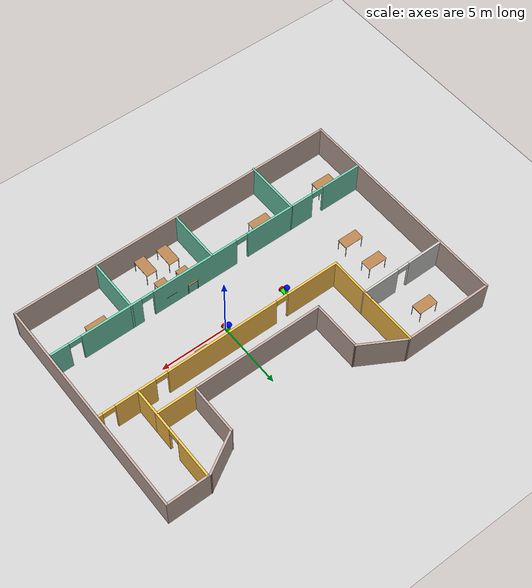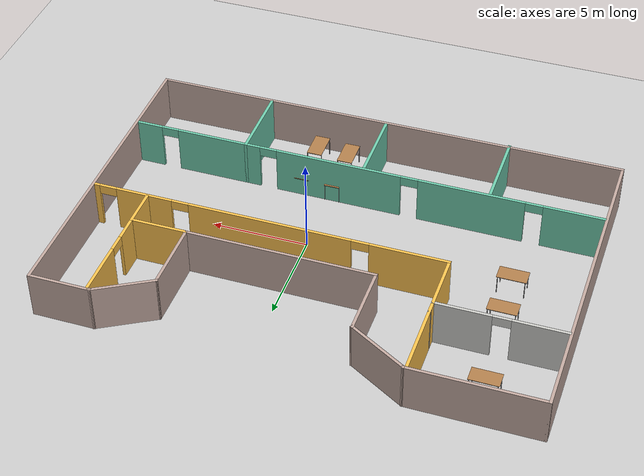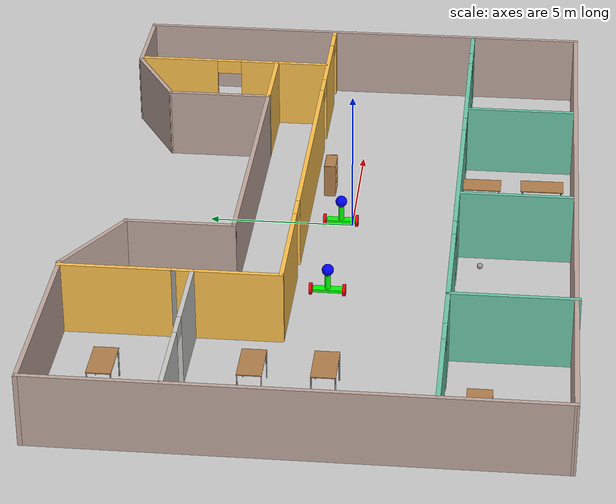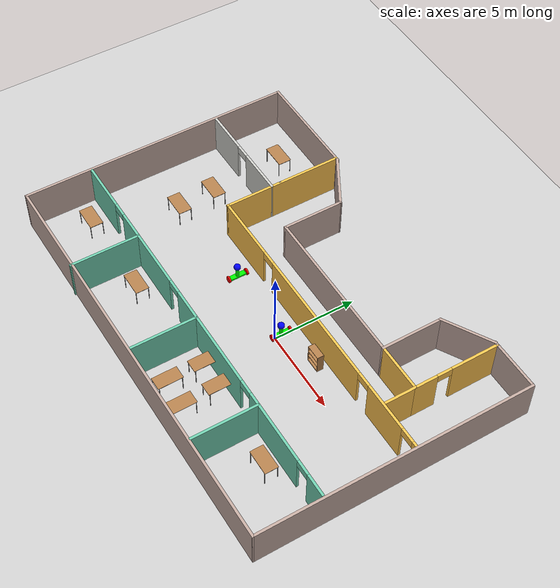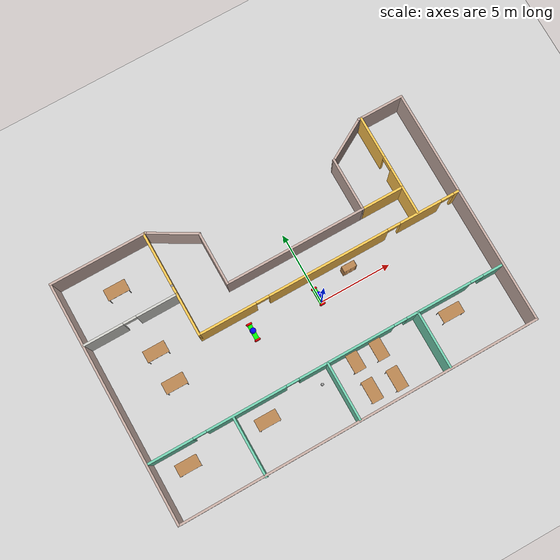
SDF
<sdf version="1.6">
 <world name="default">
  <plugin name="hello" filename="libhello.so"/>
  <light name="sun" type="directional">
   <pose>0 0 10 0 -0 0</pose>
   <diffuse>0.8 0.8 0.8 1</diffuse>
   <specular>0.2 0.2 0.2 1</specular>
   <attenuation>
    <range>1000</range>
    <constant>0.9</constant>
    <linear>0.01</linear>
    <quadratic>0.001</quadratic>
   </attenuation>
   <direction>-0.5 0.1 -0.9</direction>
  </light>
  <model name="ground_plane">
   <static>1</static>
   <link name="link">
    <collision name="collision">
     <geometry><plane><normal>0 0 1</normal><size>100 100</size></plane></geometry>
     <surface>
      <contact><collide_bitmask>65535</collide_bitmask></contact>
      <friction><ode><mu>100</mu><mu2>50</mu2></ode></friction>
     </surface>
    </collision>
    <visual name="visual">
     <cast_shadows>0</cast_shadows>
     <geometry><plane><normal>0 0 1</normal><size>100 100</size></plane></geometry>
     <material>
      <script><uri>file://media/materials/scripts/gazebo.material</uri><name>Gazebo/Grey</name></script>
     </material>
    </visual>
   </link>
  </model>
  <gravity>0 0 -9.8</gravity>
  <magnetic_field>6e-06 2.3e-05 -4.2e-05</magnetic_field>
  <atmosphere type="adiabatic"/>
  <physics name="default_physics" default="0" type="ode">
   <max_step_size>0.001</max_step_size>
   <real_time_factor>1</real_time_factor>
   <real_time_update_rate>1000</real_time_update_rate>
  </physics>
  <scene><ambient>0.4 0.4 0.4 1</ambient><background>0.7 0.7 0.7 1</background><shadows>1</shadows></scene>
  <spherical_coordinates>
   <surface_model>EARTH_WGS84</surface_model>
   <latitude_deg>0</latitude_deg>
   <longitude_deg>0</longitude_deg>
   <elevation>0</elevation>
   <heading_deg>0</heading_deg>
  </spherical_coordinates>
  <model name="table">
   <static>1</static>
   <link name="link">
    <collision name="surface">
     <pose>0 0 1 0 -0 0</pose>
     <geometry><box><size>1.5 0.8 0.03</size></box></geometry>
     <surface><friction><ode><mu>0.6</mu><mu2>0.6</mu2></ode></friction></surface>
    </collision>
    <visual name="visual1">
     <pose>0 0 1 0 -0 0</pose>
     <geometry><box><size>1.5 0.8 0.03</size></box></geometry>
     <material>
      <script><uri>file://media/materials/scripts/gazebo.material</uri><name>Gazebo/Wood</name></script>
     </material>
    </visual>
    <collision name="front_left_leg">
     <pose>0.68 0.38 0.5 0 -0 0</pose>
     <geometry><cylinder><radius>0.02</radius><length>1</length></cylinder></geometry>
    </collision>
    <visual name="front_left_leg">
     <pose>0.68 0.38 0.5 0 -0 0</pose>
     <geometry><cylinder><radius>0.02</radius><length>1</length></cylinder></geometry>
     <material>
      <script><uri>file://media/materials/scripts/gazebo.material</uri><name>Gazebo/Grey</name></script>
     </material>
    </visual>
    <collision name="front_right_leg">
     <pose>0.68 -0.38 0.5 0 -0 0</pose>
     <geometry><cylinder><radius>0.02</radius><length>1</length></cylinder></geometry>
    </collision>
    <visual name="front_right_leg">
     <pose>0.68 -0.38 0.5 0 -0 0</pose>
     <geometry><cylinder><radius>0.02</radius><length>1</length></cylinder></geometry>
     <material>
      <script><uri>file://media/materials/scripts/gazebo.material</uri><name>Gazebo/Grey</name></script>
     </material>
    </visual>
    <collision name="back_right_leg">
     <pose>-0.68 -0.38 0.5 0 -0 0</pose>
     <geometry><cylinder><radius>0.02</radius><length>1</length></cylinder></geometry>
    </collision>
    <visual name="back_right_leg">
     <pose>-0.68 -0.38 0.5 0 -0 0</pose>
     <geometry><cylinder><radius>0.02</radius><length>1</length></cylinder></geometry>
     <material>
      <script><uri>file://media/materials/scripts/gazebo.material</uri><name>Gazebo/Grey</name></script>
     </material>
    </visual>
    <collision name="back_left_leg">
     <pose>-0.68 0.38 0.5 0 -0 0</pose>
     <geometry><cylinder><radius>0.02</radius><length>1</length></cylinder></geometry>
    </collision>
    <visual name="back_left_leg">
     <pose>-0.68 0.38 0.5 0 -0 0</pose>
     <geometry><cylinder><radius>0.02</radius><length>1</length></cylinder></geometry>
     <material>
      <script><uri>file://media/materials/scripts/gazebo.material</uri><name>Gazebo/Grey</name></script>
     </material>
    </visual>
   </link>
   <pose>-10.9259 6.86543 0 0 -0 0</pose>
  </model>
  <model name="table_1">
   <static>1</static>
   <link name="link">
    <collision name="surface">
     <pose>0 0 1 0 -0 0</pose>
     <geometry><box><size>1.5 0.8 0.03</size></box></geometry>
     <surface><friction><ode><mu>0.6</mu><mu2>0.6</mu2></ode></friction></surface>
    </collision>
    <visual name="visual1">
     <pose>0 0 1 0 -0 0</pose>
     <geometry><box><size>1.5 0.8 0.03</size></box></geometry>
     <material>
      <script><uri>file://media/materials/scripts/gazebo.material</uri><name>Gazebo/Wood</name></script>
     </material>
    </visual>
    <collision name="front_left_leg">
     <pose>0.68 0.38 0.5 0 -0 0</pose>
     <geometry><cylinder><radius>0.02</radius><length>1</length></cylinder></geometry>
    </collision>
    <visual name="front_left_leg">
     <pose>0.68 0.38 0.5 0 -0 0</pose>
     <geometry><cylinder><radius>0.02</radius><length>1</length></cylinder></geometry>
     <material>
      <script><uri>file://media/materials/scripts/gazebo.material</uri><name>Gazebo/Grey</name></script>
     </material>
    </visual>
    <collision name="front_right_leg">
     <pose>0.68 -0.38 0.5 0 -0 0</pose>
     <geometry><cylinder><radius>0.02</radius><length>1</length></cylinder></geometry>
    </collision>
    <visual name="front_right_leg">
     <pose>0.68 -0.38 0.5 0 -0 0</pose>
     <geometry><cylinder><radius>0.02</radius><length>1</length></cylinder></geometry>
     <material>
      <script><uri>file://media/materials/scripts/gazebo.material</uri><name>Gazebo/Grey</name></script>
     </material>
    </visual>
    <collision name="back_right_leg">
     <pose>-0.68 -0.38 0.5 0 -0 0</pose>
     <geometry><cylinder><radius>0.02</radius><length>1</length></cylinder></geometry>
    </collision>
    <visual name="back_right_leg">
     <pose>-0.68 -0.38 0.5 0 -0 0</pose>
     <geometry><cylinder><radius>0.02</radius><length>1</length></cylinder></geometry>
     <material>
      <script><uri>file://media/materials/scripts/gazebo.material</uri><name>Gazebo/Grey</name></script>
     </material>
    </visual>
    <collision name="back_left_leg">
     <pose>-0.68 0.38 0.5 0 -0 0</pose>
     <geometry><cylinder><radius>0.02</radius><length>1</length></cylinder></geometry>
    </collision>
    <visual name="back_left_leg">
     <pose>-0.68 0.38 0.5 0 -0 0</pose>
     <geometry><cylinder><radius>0.02</radius><length>1</length></cylinder></geometry>
     <material>
      <script><uri>file://media/materials/scripts/gazebo.material</uri><name>Gazebo/Grey</name></script>
     </material>
    </visual>
   </link>
   <pose>-10.6064 2.22277 0 0 -0 0</pose>
  </model>
  <model name="table_2">
   <static>1</static>
   <link name="link">
    <collision name="surface">
     <pose>0 0 1 0 -0 0</pose>
     <geometry><box><size>1.5 0.8 0.03</size></box></geometry>
     <surface><friction><ode><mu>0.6</mu><mu2>0.6</mu2></ode></friction></surface>
    </collision>
    <visual name="visual1">
     <pose>0 0 1 0 -0 0</pose>
     <geometry><box><size>1.5 0.8 0.03</size></box></geometry>
     <material>
      <script><uri>file://media/materials/scripts/gazebo.material</uri><name>Gazebo/Wood</name></script>
     </material>
    </visual>
    <collision name="front_left_leg">
     <pose>0.68 0.38 0.5 0 -0 0</pose>
     <geometry><cylinder><radius>0.02</radius><length>1</length></cylinder></geometry>
    </collision>
    <visual name="front_left_leg">
     <pose>0.68 0.38 0.5 0 -0 0</pose>
     <geometry><cylinder><radius>0.02</radius><length>1</length></cylinder></geometry>
     <material>
      <script><uri>file://media/materials/scripts/gazebo.material</uri><name>Gazebo/Grey</name></script>
     </material>
    </visual>
    <collision name="front_right_leg">
     <pose>0.68 -0.38 0.5 0 -0 0</pose>
     <geometry><cylinder><radius>0.02</radius><length>1</length></cylinder></geometry>
    </collision>
    <visual name="front_right_leg">
     <pose>0.68 -0.38 0.5 0 -0 0</pose>
     <geometry><cylinder><radius>0.02</radius><length>1</length></cylinder></geometry>
     <material>
      <script><uri>file://media/materials/scripts/gazebo.material</uri><name>Gazebo/Grey</name></script>
     </material>
    </visual>
    <collision name="back_right_leg">
     <pose>-0.68 -0.38 0.5 0 -0 0</pose>
     <geometry><cylinder><radius>0.02</radius><length>1</length></cylinder></geometry>
    </collision>
    <visual name="back_right_leg">
     <pose>-0.68 -0.38 0.5 0 -0 0</pose>
     <geometry><cylinder><radius>0.02</radius><length>1</length></cylinder></geometry>
     <material>
      <script><uri>file://media/materials/scripts/gazebo.material</uri><name>Gazebo/Grey</name></script>
     </material>
    </visual>
    <collision name="back_left_leg">
     <pose>-0.68 0.38 0.5 0 -0 0</pose>
     <geometry><cylinder><radius>0.02</radius><length>1</length></cylinder></geometry>
    </collision>
    <visual name="back_left_leg">
     <pose>-0.68 0.38 0.5 0 -0 0</pose>
     <geometry><cylinder><radius>0.02</radius><length>1</length></cylinder></geometry>
     <material>
      <script><uri>file://media/materials/scripts/gazebo.material</uri><name>Gazebo/Grey</name></script>
     </material>
    </visual>
   </link>
   <pose>-10.5195 -0.069603 0 0 -0 0</pose>
  </model>
  <model name="table_3_clone_0">
   <static>1</static>
   <link name="link">
    <collision name="surface">
     <pose>0 0 1 0 -0 0</pose>
     <geometry><box><size>1.5 0.8 0.03</size></box></geometry>
     <surface><friction><ode><mu>0.6</mu><mu2>0.6</mu2></ode></friction></surface>
    </collision>
    <visual name="visual1">
     <pose>0 0 1 0 -0 0</pose>
     <geometry><box><size>1.5 0.8 0.03</size></box></geometry>
     <material>
      <script><uri>file://media/materials/scripts/gazebo.material</uri><name>Gazebo/Wood</name></script>
     </material>
    </visual>
    <collision name="front_left_leg">
     <pose>0.68 0.38 0.5 0 -0 0</pose>
     <geometry><cylinder><radius>0.02</radius><length>1</length></cylinder></geometry>
    </collision>
    <visual name="front_left_leg">
     <pose>0.68 0.38 0.5 0 -0 0</pose>
     <geometry><cylinder><radius>0.02</radius><length>1</length></cylinder></geometry>
     <material>
      <script><uri>file://media/materials/scripts/gazebo.material</uri><name>Gazebo/Grey</name></script>
     </material>
    </visual>
    <collision name="front_right_leg">
     <pose>0.68 -0.38 0.5 0 -0 0</pose>
     <geometry><cylinder><radius>0.02</radius><length>1</length></cylinder></geometry>
    </collision>
    <visual name="front_right_leg">
     <pose>0.68 -0.38 0.5 0 -0 0</pose>
     <geometry><cylinder><radius>0.02</radius><length>1</length></cylinder></geometry>
     <material>
      <script><uri>file://media/materials/scripts/gazebo.material</uri><name>Gazebo/Grey</name></script>
     </material>
    </visual>
    <collision name="back_right_leg">
     <pose>-0.68 -0.38 0.5 0 -0 0</pose>
     <geometry><cylinder><radius>0.02</radius><length>1</length></cylinder></geometry>
    </collision>
    <visual name="back_right_leg">
     <pose>-0.68 -0.38 0.5 0 -0 0</pose>
     <geometry><cylinder><radius>0.02</radius><length>1</length></cylinder></geometry>
     <material>
      <script><uri>file://media/materials/scripts/gazebo.material</uri><name>Gazebo/Grey</name></script>
     </material>
    </visual>
    <collision name="back_left_leg">
     <pose>-0.68 0.38 0.5 0 -0 0</pose>
     <geometry><cylinder><radius>0.02</radius><length>1</length></cylinder></geometry>
    </collision>
    <visual name="back_left_leg">
     <pose>-0.68 0.38 0.5 0 -0 0</pose>
     <geometry><cylinder><radius>0.02</radius><length>1</length></cylinder></geometry>
     <material>
      <script><uri>file://media/materials/scripts/gazebo.material</uri><name>Gazebo/Grey</name></script>
     </material>
    </visual>
   </link>
   <pose>-0.106146 -4.31768 0 0 0 -1.56564</pose>
  </model>
  <model name="table_3_clone_1">
   <static>1</static>
   <link name="link">
    <collision name="surface">
     <pose>0 0 1 0 -0 0</pose>
     <geometry><box><size>1.5 0.8 0.03</size></box></geometry>
     <surface><friction><ode><mu>0.6</mu><mu2>0.6</mu2></ode></friction></surface>
    </collision>
    <visual name="visual1">
     <pose>0 0 1 0 -0 0</pose>
     <geometry><box><size>1.5 0.8 0.03</size></box></geometry>
     <material>
      <script><uri>file://media/materials/scripts/gazebo.material</uri><name>Gazebo/Wood</name></script>
     </material>
    </visual>
    <collision name="front_left_leg">
     <pose>0.68 0.38 0.5 0 -0 0</pose>
     <geometry><cylinder><radius>0.02</radius><length>1</length></cylinder></geometry>
    </collision>
    <visual name="front_left_leg">
     <pose>0.68 0.38 0.5 0 -0 0</pose>
     <geometry><cylinder><radius>0.02</radius><length>1</length></cylinder></geometry>
     <material>
      <script><uri>file://media/materials/scripts/gazebo.material</uri><name>Gazebo/Grey</name></script>
     </material>
    </visual>
    <collision name="front_right_leg">
     <pose>0.68 -0.38 0.5 0 -0 0</pose>
     <geometry><cylinder><radius>0.02</radius><length>1</length></cylinder></geometry>
    </collision>
    <visual name="front_right_leg">
     <pose>0.68 -0.38 0.5 0 -0 0</pose>
     <geometry><cylinder><radius>0.02</radius><length>1</length></cylinder></geometry>
     <material>
      <script><uri>file://media/materials/scripts/gazebo.material</uri><name>Gazebo/Grey</name></script>
     </material>
    </visual>
    <collision name="back_right_leg">
     <pose>-0.68 -0.38 0.5 0 -0 0</pose>
     <geometry><cylinder><radius>0.02</radius><length>1</length></cylinder></geometry>
    </collision>
    <visual name="back_right_leg">
     <pose>-0.68 -0.38 0.5 0 -0 0</pose>
     <geometry><cylinder><radius>0.02</radius><length>1</length></cylinder></geometry>
     <material>
      <script><uri>file://media/materials/scripts/gazebo.material</uri><name>Gazebo/Grey</name></script>
     </material>
    </visual>
    <collision name="back_left_leg">
     <pose>-0.68 0.38 0.5 0 -0 0</pose>
     <geometry><cylinder><radius>0.02</radius><length>1</length></cylinder></geometry>
    </collision>
    <visual name="back_left_leg">
     <pose>-0.68 0.38 0.5 0 -0 0</pose>
     <geometry><cylinder><radius>0.02</radius><length>1</length></cylinder></geometry>
     <material>
      <script><uri>file://media/materials/scripts/gazebo.material</uri><name>Gazebo/Grey</name></script>
     </material>
    </visual>
   </link>
   <pose>1.55412 -4.38959 0 0 0 -1.56564</pose>
  </model>
  <model name="table_3_clone_4">
   <static>1</static>
   <link name="link">
    <collision name="surface">
     <pose>0 0 1 0 -0 0</pose>
     <geometry><box><size>1.5 0.8 0.03</size></box></geometry>
     <surface><friction><ode><mu>0.6</mu><mu2>0.6</mu2></ode></friction></surface>
    </collision>
    <visual name="visual1">
     <pose>0 0 1 0 -0 0</pose>
     <geometry><box><size>1.5 0.8 0.03</size></box></geometry>
     <material>
      <script><uri>file://media/materials/scripts/gazebo.material</uri><name>Gazebo/Wood</name></script>
     </material>
    </visual>
    <collision name="front_left_leg">
     <pose>0.68 0.38 0.5 0 -0 0</pose>
     <geometry><cylinder><radius>0.02</radius><length>1</length></cylinder></geometry>
    </collision>
    <visual name="front_left_leg">
     <pose>0.68 0.38 0.5 0 -0 0</pose>
     <geometry><cylinder><radius>0.02</radius><length>1</length></cylinder></geometry>
     <material>
      <script><uri>file://media/materials/scripts/gazebo.material</uri><name>Gazebo/Grey</name></script>
     </material>
    </visual>
    <collision name="front_right_leg">
     <pose>0.68 -0.38 0.5 0 -0 0</pose>
     <geometry><cylinder><radius>0.02</radius><length>1</length></cylinder></geometry>
    </collision>
    <visual name="front_right_leg">
     <pose>0.68 -0.38 0.5 0 -0 0</pose>
     <geometry><cylinder><radius>0.02</radius><length>1</length></cylinder></geometry>
     <material>
      <script><uri>file://media/materials/scripts/gazebo.material</uri><name>Gazebo/Grey</name></script>
     </material>
    </visual>
    <collision name="back_right_leg">
     <pose>-0.68 -0.38 0.5 0 -0 0</pose>
     <geometry><cylinder><radius>0.02</radius><length>1</length></cylinder></geometry>
    </collision>
    <visual name="back_right_leg">
     <pose>-0.68 -0.38 0.5 0 -0 0</pose>
     <geometry><cylinder><radius>0.02</radius><length>1</length></cylinder></geometry>
     <material>
      <script><uri>file://media/materials/scripts/gazebo.material</uri><name>Gazebo/Grey</name></script>
     </material>
    </visual>
    <collision name="back_left_leg">
     <pose>-0.68 0.38 0.5 0 -0 0</pose>
     <geometry><cylinder><radius>0.02</radius><length>1</length></cylinder></geometry>
    </collision>
    <visual name="back_left_leg">
     <pose>-0.68 0.38 0.5 0 -0 0</pose>
     <geometry><cylinder><radius>0.02</radius><length>1</length></cylinder></geometry>
     <material>
      <script><uri>file://media/materials/scripts/gazebo.material</uri><name>Gazebo/Grey</name></script>
     </material>
    </visual>
   </link>
   <pose>-0.09497 -6.45475 0 0 0 -1.56564</pose>
  </model>
  <model name="table_3_clone_5">
   <static>1</static>
   <link name="link">
    <collision name="surface">
     <pose>0 0 1 0 -0 0</pose>
     <geometry><box><size>1.5 0.8 0.03</size></box></geometry>
     <surface><friction><ode><mu>0.6</mu><mu2>0.6</mu2></ode></friction></surface>
    </collision>
    <visual name="visual1">
     <pose>0 0 1 0 -0 0</pose>
     <geometry><box><size>1.5 0.8 0.03</size></box></geometry>
     <material>
      <script><uri>file://media/materials/scripts/gazebo.material</uri><name>Gazebo/Wood</name></script>
     </material>
    </visual>
    <collision name="front_left_leg">
     <pose>0.68 0.38 0.5 0 -0 0</pose>
     <geometry><cylinder><radius>0.02</radius><length>1</length></cylinder></geometry>
    </collision>
    <visual name="front_left_leg">
     <pose>0.68 0.38 0.5 0 -0 0</pose>
     <geometry><cylinder><radius>0.02</radius><length>1</length></cylinder></geometry>
     <material>
      <script><uri>file://media/materials/scripts/gazebo.material</uri><name>Gazebo/Grey</name></script>
     </material>
    </visual>
    <collision name="front_right_leg">
     <pose>0.68 -0.38 0.5 0 -0 0</pose>
     <geometry><cylinder><radius>0.02</radius><length>1</length></cylinder></geometry>
    </collision>
    <visual name="front_right_leg">
     <pose>0.68 -0.38 0.5 0 -0 0</pose>
     <geometry><cylinder><radius>0.02</radius><length>1</length></cylinder></geometry>
     <material>
      <script><uri>file://media/materials/scripts/gazebo.material</uri><name>Gazebo/Grey</name></script>
     </material>
    </visual>
    <collision name="back_right_leg">
     <pose>-0.68 -0.38 0.5 0 -0 0</pose>
     <geometry><cylinder><radius>0.02</radius><length>1</length></cylinder></geometry>
    </collision>
    <visual name="back_right_leg">
     <pose>-0.68 -0.38 0.5 0 -0 0</pose>
     <geometry><cylinder><radius>0.02</radius><length>1</length></cylinder></geometry>
     <material>
      <script><uri>file://media/materials/scripts/gazebo.material</uri><name>Gazebo/Grey</name></script>
     </material>
    </visual>
    <collision name="back_left_leg">
     <pose>-0.68 0.38 0.5 0 -0 0</pose>
     <geometry><cylinder><radius>0.02</radius><length>1</length></cylinder></geometry>
    </collision>
    <visual name="back_left_leg">
     <pose>-0.68 0.38 0.5 0 -0 0</pose>
     <geometry><cylinder><radius>0.02</radius><length>1</length></cylinder></geometry>
     <material>
      <script><uri>file://media/materials/scripts/gazebo.material</uri><name>Gazebo/Grey</name></script>
     </material>
    </visual>
   </link>
   <pose>1.61469 -6.58432 0 0 0 -1.56564</pose>
  </model>
  <model name="RobotModel">
   <link name="link_0">
    <pose>0 0 0.2 0 -0 0</pose>
    <inertial>
     <mass>1</mass>
     <inertia>
      <ixx>0.166667</ixx>
      <ixy>0</ixy>
      <ixz>0</ixz>
      <iyy>0.166667</iyy>
      <iyz>0</iyz>
      <izz>0.166667</izz>
     </inertia>
    </inertial>
    <visual name="visual">
     <geometry><box><size>0.3 1 0.1</size></box></geometry>
     <material>
      <lighting>1</lighting>
      <script><uri>file://media/materials/scripts/gazebo.material</uri><name>Gazebo/Grey</name></script>
      <ambient>0 1 0 1</ambient>
      <diffuse>0.7 0.7 0.7 1</diffuse>
      <specular>0.01 0.01 0.01 1</specular>
      <emissive>0 0 0 1</emissive>
      <shader type="vertex"><normal_map>__default__</normal_map></shader>
     </material>
    </visual>
    <collision name="collision">
     <geometry><box><size>0.3 1 0.1</size></box></geometry>
     <surface>
      <friction>
       <ode><mu>1</mu><mu2>1</mu2><fdir1>0 0 0</fdir1><slip1>0</slip1><slip2>0</slip2></ode>
       <torsional>
        <coefficient>1</coefficient>
        <patch_radius>0</patch_radius>
        <surface_radius>0</surface_radius>
        <use_patch_radius>1</use_patch_radius>
        <ode><slip>0</slip></ode>
       </torsional>
      </friction>
      <bounce><restitution_coefficient>0</restitution_coefficient><threshold>1e+06</threshold></bounce>
      <contact>
       <collide_without_contact>0</collide_without_contact>
       <collide_without_contact_bitmask>1</collide_without_contact_bitmask>
       <collide_bitmask>1</collide_bitmask>
       <ode>
        <soft_cfm>0</soft_cfm>
        <soft_erp>0.2</soft_erp>
        <kp>1e+13</kp>
        <kd>1</kd>
        <max_vel>0.01</max_vel>
        <min_depth>0</min_depth>
       </ode>
       <bullet>
        <split_impulse>1</split_impulse>
        <split_impulse_penetration_threshold>-0.01</split_impulse_penetration_threshold>
        <soft_cfm>0</soft_cfm>
        <soft_erp>0.2</soft_erp>
        <kp>1e+13</kp>
        <kd>1</kd>
       </bullet>
      </contact>
     </surface>
    </collision>
   </link>
   <link name="link_1">
    <pose>0 -0.550023 0.200016 1.5707 -0 0</pose>
    <inertial>
     <mass>1</mass>
     <inertia><ixx>0.145833</ixx><ixy>0</ixy><ixz>0</ixz><iyy>0.145833</iyy><iyz>0</iyz><izz>0.125</izz></inertia>
    </inertial>
    <visual name="visual">
     <geometry><cylinder><radius>0.2</radius><length>0.1</length></cylinder></geometry>
     <material>
      <lighting>1</lighting>
      <script><uri>file://media/materials/scripts/gazebo.material</uri><name>Gazebo/Grey</name></script>
      <ambient>1 0 0 1</ambient>
      <diffuse>0.7 0.7 0.7 1</diffuse>
      <specular>0.01 0.01 0.01 1</specular>
      <emissive>0 0 0 1</emissive>
      <shader type="vertex"><normal_map>__default__</normal_map></shader>
     </material>
    </visual>
    <collision name="collision">
     <geometry><cylinder><radius>0.2</radius><length>0.1</length></cylinder></geometry>
     <surface>
      <friction>
       <ode><mu>1</mu><mu2>1</mu2><fdir1>0 0 0</fdir1><slip1>0</slip1><slip2>0</slip2></ode>
       <torsional>
        <coefficient>1</coefficient>
        <patch_radius>0</patch_radius>
        <surface_radius>0</surface_radius>
        <use_patch_radius>1</use_patch_radius>
        <ode><slip>0</slip></ode>
       </torsional>
      </friction>
      <bounce><restitution_coefficient>0</restitution_coefficient><threshold>1e+06</threshold></bounce>
      <contact>
       <collide_without_contact>0</collide_without_contact>
       <collide_without_contact_bitmask>1</collide_without_contact_bitmask>
       <collide_bitmask>1</collide_bitmask>
       <ode>
        <soft_cfm>0</soft_cfm>
        <soft_erp>0.2</soft_erp>
        <kp>1e+13</kp>
        <kd>1</kd>
        <max_vel>0.01</max_vel>
        <min_depth>0</min_depth>
       </ode>
       <bullet>
        <split_impulse>1</split_impulse>
        <split_impulse_penetration_threshold>-0.01</split_impulse_penetration_threshold>
        <soft_cfm>0</soft_cfm>
        <soft_erp>0.2</soft_erp>
        <kp>1e+13</kp>
        <kd>1</kd>
       </bullet>
      </contact>
     </surface>
    </collision>
   </link>
   <link name="link_1_clone">
    <pose>0 0.580446 0.200008 1.57071 -0 0</pose>
    <inertial>
     <mass>1</mass>
     <inertia><ixx>0.145833</ixx><ixy>0</ixy><ixz>0</ixz><iyy>0.145833</iyy><iyz>0</iyz><izz>0.125</izz></inertia>
    </inertial>
    <visual name="visual">
     <geometry><cylinder><radius>0.2</radius><length>0.1</length></cylinder></geometry>
     <material>
      <lighting>1</lighting>
      <script><uri>file://media/materials/scripts/gazebo.material</uri><name>Gazebo/Grey</name></script>
      <ambient>1 0 0 1</ambient>
      <diffuse>0.7 0.7 0.7 1</diffuse>
      <specular>0.01 0.01 0.01 1</specular>
      <emissive>0 0 0 1</emissive>
      <shader type="vertex"><normal_map>__default__</normal_map></shader>
     </material>
    </visual>
    <collision name="collision">
     <geometry><cylinder><radius>0.2</radius><length>0.1</length></cylinder></geometry>
     <surface>
      <friction>
       <ode><mu>1</mu><mu2>1</mu2><fdir1>0 0 0</fdir1><slip1>0</slip1><slip2>0</slip2></ode>
       <torsional>
        <coefficient>1</coefficient>
        <patch_radius>0</patch_radius>
        <surface_radius>0</surface_radius>
        <use_patch_radius>1</use_patch_radius>
        <ode><slip>0</slip></ode>
       </torsional>
      </friction>
      <bounce><restitution_coefficient>0</restitution_coefficient><threshold>1e+06</threshold></bounce>
      <contact>
       <collide_without_contact>0</collide_without_contact>
       <collide_without_contact_bitmask>1</collide_without_contact_bitmask>
       <collide_bitmask>1</collide_bitmask>
       <ode>
        <soft_cfm>0</soft_cfm>
        <soft_erp>0.2</soft_erp>
        <kp>1e+13</kp>
        <kd>1</kd>
        <max_vel>0.01</max_vel>
        <min_depth>0</min_depth>
       </ode>
       <bullet>
        <split_impulse>1</split_impulse>
        <split_impulse_penetration_threshold>-0.01</split_impulse_penetration_threshold>
        <soft_cfm>0</soft_cfm>
        <soft_erp>0.2</soft_erp>
        <kp>1e+13</kp>
        <kd>1</kd>
       </bullet>
      </contact>
     </surface>
    </collision>
   </link>
   <link name="link_2">
    <pose>0 0 0.5 0 -0 0</pose>
    <inertial>
     <mass>1</mass>
     <inertia><ixx>0.145833</ixx><ixy>0</ixy><ixz>0</ixz><iyy>0.145833</iyy><iyz>0</iyz><izz>0.125</izz></inertia>
    </inertial>
    <visual name="visual">
     <geometry><cylinder><radius>0.1</radius><length>0.5</length></cylinder></geometry>
     <material>
      <lighting>1</lighting>
      <script><uri>file://media/materials/scripts/gazebo.material</uri><name>Gazebo/Grey</name></script>
      <shader type="pixel"><normal_map>__default__</normal_map></shader>
      <ambient>0 1 0 1</ambient>
      <diffuse>0.7 0.7 0.7 1</diffuse>
      <specular>0.01 0.01 0.01 1</specular>
      <emissive>0 0 0 1</emissive>
     </material>
    </visual>
    <collision name="collision">
     <geometry><cylinder><radius>0.1</radius><length>0.5</length></cylinder></geometry>
     <surface>
      <friction>
       <ode><mu>1</mu><mu2>1</mu2><fdir1>0 0 0</fdir1><slip1>0</slip1><slip2>0</slip2></ode>
       <torsional>
        <coefficient>1</coefficient>
        <patch_radius>0</patch_radius>
        <surface_radius>0</surface_radius>
        <use_patch_radius>1</use_patch_radius>
        <ode><slip>0</slip></ode>
       </torsional>
      </friction>
      <bounce><restitution_coefficient>0</restitution_coefficient><threshold>1e+06</threshold></bounce>
      <contact>
       <collide_without_contact>0</collide_without_contact>
       <collide_without_contact_bitmask>1</collide_without_contact_bitmask>
       <collide_bitmask>1</collide_bitmask>
       <ode>
        <soft_cfm>0</soft_cfm>
        <soft_erp>0.2</soft_erp>
        <kp>1e+13</kp>
        <kd>1</kd>
        <max_vel>0.01</max_vel>
        <min_depth>0</min_depth>
       </ode>
       <bullet>
        <split_impulse>1</split_impulse>
        <split_impulse_penetration_threshold>-0.01</split_impulse_penetration_threshold>
        <soft_cfm>0</soft_cfm>
        <soft_erp>0.2</soft_erp>
        <kp>1e+13</kp>
        <kd>1</kd>
       </bullet>
      </contact>
     </surface>
    </collision>
   </link>
   <link name="link_3">
    <pose>0 -0 0.95 0 -0 0</pose>
    <inertial>
     <mass>1</mass>
     <inertia><ixx>0.1</ixx><ixy>0</ixy><ixz>0</ixz><iyy>0.1</iyy><iyz>0</iyz><izz>0.1</izz></inertia>
    </inertial>
    <visual name="visual">
     <geometry><sphere><radius>0.2</radius></sphere></geometry>
     <material>
      <lighting>1</lighting>
      <script><uri>file://media/materials/scripts/gazebo.material</uri><name>Gazebo/Grey</name></script>
      <shader type="pixel"><normal_map>__default__</normal_map></shader>
      <ambient>0 0 1 1</ambient>
      <diffuse>0.7 0.7 0.7 1</diffuse>
      <specular>0.01 0.01 0.01 1</specular>
      <emissive>0 0 0 1</emissive>
     </material>
    </visual>
    <collision name="collision">
     <geometry><sphere><radius>0.2</radius></sphere></geometry>
     <surface>
      <friction>
       <ode><mu>1</mu><mu2>1</mu2><fdir1>0 0 0</fdir1><slip1>0</slip1><slip2>0</slip2></ode>
       <torsional>
        <coefficient>1</coefficient>
        <patch_radius>0</patch_radius>
        <surface_radius>0</surface_radius>
        <use_patch_radius>1</use_patch_radius>
        <ode><slip>0</slip></ode>
       </torsional>
      </friction>
      <bounce><restitution_coefficient>0</restitution_coefficient><threshold>1e+06</threshold></bounce>
      <contact>
       <collide_without_contact>0</collide_without_contact>
       <collide_without_contact_bitmask>1</collide_without_contact_bitmask>
       <collide_bitmask>1</collide_bitmask>
       <ode>
        <soft_cfm>0</soft_cfm>
        <soft_erp>0.2</soft_erp>
        <kp>1e+13</kp>
        <kd>1</kd>
        <max_vel>0.01</max_vel>
        <min_depth>0</min_depth>
       </ode>
       <bullet>
        <split_impulse>1</split_impulse>
        <split_impulse_penetration_threshold>-0.01</split_impulse_penetration_threshold>
        <soft_cfm>0</soft_cfm>
        <soft_erp>0.2</soft_erp>
        <kp>1e+13</kp>
        <kd>1</kd>
       </bullet>
      </contact>
     </surface>
    </collision>
   </link>
   <joint name="link_0_JOINT_0" type="revolute">
    <parent>link_0</parent>
    <child>link_1</child>
    <axis>
     <xyz>0 0 1</xyz>
     <use_parent_model_frame>0</use_parent_model_frame>
     <limit>
      <lower>-1.79769e+308</lower>
      <upper>1.79769e+308</upper>
      <effort>-1</effort>
      <velocity>-1</velocity>
     </limit>
     <dynamics>
      <spring_reference>0</spring_reference>
      <spring_stiffness>0</spring_stiffness>
      <damping>0</damping>
      <friction>0</friction>
     </dynamics>
    </axis>
    <physics>
     <ode><limit><cfm>0</cfm><erp>0.2</erp></limit><suspension><cfm>0</cfm><erp>0.2</erp></suspension></ode>
    </physics>
   </joint>
   <joint name="link_0_JOINT_1" type="revolute">
    <parent>link_0</parent>
    <child>link_1_clone</child>
    <axis>
     <xyz>0 0 1</xyz>
     <use_parent_model_frame>0</use_parent_model_frame>
     <limit>
      <lower>-1.79769e+308</lower>
      <upper>1.79769e+308</upper>
      <effort>-1</effort>
      <velocity>-1</velocity>
     </limit>
     <dynamics>
      <spring_reference>0</spring_reference>
      <spring_stiffness>0</spring_stiffness>
      <damping>0</damping>
     </dynamics>
    </axis>
    <physics>
     <ode><limit><cfm>0</cfm><erp>0.2</erp></limit><suspension><cfm>0</cfm><erp>0.2</erp></suspension></ode>
    </physics>
   </joint>
   <joint name="link_2_JOINT_2" type="revolute">
    <parent>link_0</parent>
    <child>link_2</child>
    <axis>
     <xyz>0 0 1</xyz>
     <use_parent_model_frame>0</use_parent_model_frame>
     <limit>
      <lower>-1.79769e+308</lower>
      <upper>1.79769e+308</upper>
      <effort>-1</effort>
      <velocity>-1</velocity>
     </limit>
     <dynamics>
      <spring_reference>0</spring_reference>
      <spring_stiffness>0</spring_stiffness>
      <damping>0</damping>
     </dynamics>
    </axis>
    <physics>
     <ode><limit><cfm>0</cfm><erp>0.2</erp></limit><suspension><cfm>0</cfm><erp>0.2</erp></suspension></ode>
    </physics>
   </joint>
   <joint name="link_2_JOINT_3" type="revolute">
    <parent>link_2</parent>
    <child>link_3</child>
    <axis>
     <xyz>0 0 1</xyz>
     <use_parent_model_frame>0</use_parent_model_frame>
     <limit>
      <lower>-1.79769e+308</lower>
      <upper>1.79769e+308</upper>
      <effort>-1</effort>
      <velocity>-1</velocity>
     </limit>
     <dynamics>
      <spring_reference>0</spring_reference>
      <spring_stiffness>0</spring_stiffness>
      <damping>0</damping>
     </dynamics>
    </axis>
    <physics>
     <ode><limit><cfm>0</cfm><erp>0.2</erp></limit><suspension><cfm>0</cfm><erp>0.2</erp></suspension></ode>
    </physics>
   </joint>
   <static>0</static>
   <pose>0 0.3896 -8e-06 7e-06 -0 0</pose>
  </model>
  <model name="RobotModel_clone">
   <link name="link_0">
    <pose>0 0 0.2 0 -0 0</pose>
    <inertial>
     <mass>1</mass>
     <inertia>
      <ixx>0.166667</ixx>
      <ixy>0</ixy>
      <ixz>0</ixz>
      <iyy>0.166667</iyy>
      <iyz>0</iyz>
      <izz>0.166667</izz>
     </inertia>
    </inertial>
    <visual name="visual">
     <geometry><box><size>0.3 1 0.1</size></box></geometry>
     <material>
      <lighting>1</lighting>
      <script><uri>file://media/materials/scripts/gazebo.material</uri><name>Gazebo/Grey</name></script>
      <ambient>0 1 0 1</ambient>
      <diffuse>0.7 0.7 0.7 1</diffuse>
      <specular>0.01 0.01 0.01 1</specular>
      <emissive>0 0 0 1</emissive>
      <shader type="vertex"><normal_map>__default__</normal_map></shader>
     </material>
    </visual>
    <collision name="collision">
     <geometry><box><size>0.3 1 0.1</size></box></geometry>
     <surface>
      <friction>
       <ode><mu>1</mu><mu2>1</mu2><fdir1>0 0 0</fdir1><slip1>0</slip1><slip2>0</slip2></ode>
       <torsional>
        <coefficient>1</coefficient>
        <patch_radius>0</patch_radius>
        <surface_radius>0</surface_radius>
        <use_patch_radius>1</use_patch_radius>
        <ode><slip>0</slip></ode>
       </torsional>
      </friction>
      <bounce><restitution_coefficient>0</restitution_coefficient><threshold>1e+06</threshold></bounce>
      <contact>
       <collide_without_contact>0</collide_without_contact>
       <collide_without_contact_bitmask>1</collide_without_contact_bitmask>
       <collide_bitmask>1</collide_bitmask>
       <ode>
        <soft_cfm>0</soft_cfm>
        <soft_erp>0.2</soft_erp>
        <kp>1e+13</kp>
        <kd>1</kd>
        <max_vel>0.01</max_vel>
        <min_depth>0</min_depth>
       </ode>
       <bullet>
        <split_impulse>1</split_impulse>
        <split_impulse_penetration_threshold>-0.01</split_impulse_penetration_threshold>
        <soft_cfm>0</soft_cfm>
        <soft_erp>0.2</soft_erp>
        <kp>1e+13</kp>
        <kd>1</kd>
       </bullet>
      </contact>
     </surface>
    </collision>
   </link>
   <link name="link_1">
    <pose>0 -0.550023 0.200016 1.5707 -0 0</pose>
    <inertial>
     <mass>1</mass>
     <inertia><ixx>0.145833</ixx><ixy>0</ixy><ixz>0</ixz><iyy>0.145833</iyy><iyz>0</iyz><izz>0.125</izz></inertia>
    </inertial>
    <visual name="visual">
     <geometry><cylinder><radius>0.2</radius><length>0.1</length></cylinder></geometry>
     <material>
      <lighting>1</lighting>
      <script><uri>file://media/materials/scripts/gazebo.material</uri><name>Gazebo/Grey</name></script>
      <ambient>1 0 0 1</ambient>
      <diffuse>0.7 0.7 0.7 1</diffuse>
      <specular>0.01 0.01 0.01 1</specular>
      <emissive>0 0 0 1</emissive>
      <shader type="vertex"><normal_map>__default__</normal_map></shader>
     </material>
    </visual>
    <collision name="collision">
     <geometry><cylinder><radius>0.2</radius><length>0.1</length></cylinder></geometry>
     <surface>
      <friction>
       <ode><mu>1</mu><mu2>1</mu2><fdir1>0 0 0</fdir1><slip1>0</slip1><slip2>0</slip2></ode>
       <torsional>
        <coefficient>1</coefficient>
        <patch_radius>0</patch_radius>
        <surface_radius>0</surface_radius>
        <use_patch_radius>1</use_patch_radius>
        <ode><slip>0</slip></ode>
       </torsional>
      </friction>
      <bounce><restitution_coefficient>0</restitution_coefficient><threshold>1e+06</threshold></bounce>
      <contact>
       <collide_without_contact>0</collide_without_contact>
       <collide_without_contact_bitmask>1</collide_without_contact_bitmask>
       <collide_bitmask>1</collide_bitmask>
       <ode>
        <soft_cfm>0</soft_cfm>
        <soft_erp>0.2</soft_erp>
        <kp>1e+13</kp>
        <kd>1</kd>
        <max_vel>0.01</max_vel>
        <min_depth>0</min_depth>
       </ode>
       <bullet>
        <split_impulse>1</split_impulse>
        <split_impulse_penetration_threshold>-0.01</split_impulse_penetration_threshold>
        <soft_cfm>0</soft_cfm>
        <soft_erp>0.2</soft_erp>
        <kp>1e+13</kp>
        <kd>1</kd>
       </bullet>
      </contact>
     </surface>
    </collision>
   </link>
   <link name="link_1_clone">
    <pose>0 0.580446 0.200008 1.57071 -0 0</pose>
    <inertial>
     <mass>1</mass>
     <inertia><ixx>0.145833</ixx><ixy>0</ixy><ixz>0</ixz><iyy>0.145833</iyy><iyz>0</iyz><izz>0.125</izz></inertia>
    </inertial>
    <visual name="visual">
     <geometry><cylinder><radius>0.2</radius><length>0.1</length></cylinder></geometry>
     <material>
      <lighting>1</lighting>
      <script><uri>file://media/materials/scripts/gazebo.material</uri><name>Gazebo/Grey</name></script>
      <ambient>1 0 0 1</ambient>
      <diffuse>0.7 0.7 0.7 1</diffuse>
      <specular>0.01 0.01 0.01 1</specular>
      <emissive>0 0 0 1</emissive>
      <shader type="vertex"><normal_map>__default__</normal_map></shader>
     </material>
    </visual>
    <collision name="collision">
     <geometry><cylinder><radius>0.2</radius><length>0.1</length></cylinder></geometry>
     <surface>
      <friction>
       <ode><mu>1</mu><mu2>1</mu2><fdir1>0 0 0</fdir1><slip1>0</slip1><slip2>0</slip2></ode>
       <torsional>
        <coefficient>1</coefficient>
        <patch_radius>0</patch_radius>
        <surface_radius>0</surface_radius>
        <use_patch_radius>1</use_patch_radius>
        <ode><slip>0</slip></ode>
       </torsional>
      </friction>
      <bounce><restitution_coefficient>0</restitution_coefficient><threshold>1e+06</threshold></bounce>
      <contact>
       <collide_without_contact>0</collide_without_contact>
       <collide_without_contact_bitmask>1</collide_without_contact_bitmask>
       <collide_bitmask>1</collide_bitmask>
       <ode>
        <soft_cfm>0</soft_cfm>
        <soft_erp>0.2</soft_erp>
        <kp>1e+13</kp>
        <kd>1</kd>
        <max_vel>0.01</max_vel>
        <min_depth>0</min_depth>
       </ode>
       <bullet>
        <split_impulse>1</split_impulse>
        <split_impulse_penetration_threshold>-0.01</split_impulse_penetration_threshold>
        <soft_cfm>0</soft_cfm>
        <soft_erp>0.2</soft_erp>
        <kp>1e+13</kp>
        <kd>1</kd>
       </bullet>
      </contact>
     </surface>
    </collision>
   </link>
   <link name="link_2">
    <pose>0 0 0.5 0 -0 0</pose>
    <inertial>
     <mass>1</mass>
     <inertia><ixx>0.145833</ixx><ixy>0</ixy><ixz>0</ixz><iyy>0.145833</iyy><iyz>0</iyz><izz>0.125</izz></inertia>
    </inertial>
    <visual name="visual">
     <geometry><cylinder><radius>0.1</radius><length>0.5</length></cylinder></geometry>
     <material>
      <lighting>1</lighting>
      <script><uri>file://media/materials/scripts/gazebo.material</uri><name>Gazebo/Grey</name></script>
      <shader type="pixel"><normal_map>__default__</normal_map></shader>
      <ambient>0 1 0 1</ambient>
      <diffuse>0.7 0.7 0.7 1</diffuse>
      <specular>0.01 0.01 0.01 1</specular>
      <emissive>0 0 0 1</emissive>
     </material>
    </visual>
    <collision name="collision">
     <geometry><cylinder><radius>0.1</radius><length>0.5</length></cylinder></geometry>
     <surface>
      <friction>
       <ode><mu>1</mu><mu2>1</mu2><fdir1>0 0 0</fdir1><slip1>0</slip1><slip2>0</slip2></ode>
       <torsional>
        <coefficient>1</coefficient>
        <patch_radius>0</patch_radius>
        <surface_radius>0</surface_radius>
        <use_patch_radius>1</use_patch_radius>
        <ode><slip>0</slip></ode>
       </torsional>
      </friction>
      <bounce><restitution_coefficient>0</restitution_coefficient><threshold>1e+06</threshold></bounce>
      <contact>
       <collide_without_contact>0</collide_without_contact>
       <collide_without_contact_bitmask>1</collide_without_contact_bitmask>
       <collide_bitmask>1</collide_bitmask>
       <ode>
        <soft_cfm>0</soft_cfm>
        <soft_erp>0.2</soft_erp>
        <kp>1e+13</kp>
        <kd>1</kd>
        <max_vel>0.01</max_vel>
        <min_depth>0</min_depth>
       </ode>
       <bullet>
        <split_impulse>1</split_impulse>
        <split_impulse_penetration_threshold>-0.01</split_impulse_penetration_threshold>
        <soft_cfm>0</soft_cfm>
        <soft_erp>0.2</soft_erp>
        <kp>1e+13</kp>
        <kd>1</kd>
       </bullet>
      </contact>
     </surface>
    </collision>
   </link>
   <link name="link_3">
    <pose>0 -0 0.95 0 -0 0</pose>
    <inertial>
     <mass>1</mass>
     <inertia><ixx>0.1</ixx><ixy>0</ixy><ixz>0</ixz><iyy>0.1</iyy><iyz>0</iyz><izz>0.1</izz></inertia>
    </inertial>
    <visual name="visual">
     <geometry><sphere><radius>0.2</radius></sphere></geometry>
     <material>
      <lighting>1</lighting>
      <script><uri>file://media/materials/scripts/gazebo.material</uri><name>Gazebo/Grey</name></script>
      <shader type="pixel"><normal_map>__default__</normal_map></shader>
      <ambient>0 0 1 1</ambient>
      <diffuse>0.7 0.7 0.7 1</diffuse>
      <specular>0.01 0.01 0.01 1</specular>
      <emissive>0 0 0 1</emissive>
     </material>
    </visual>
    <collision name="collision">
     <geometry><sphere><radius>0.2</radius></sphere></geometry>
     <surface>
      <friction>
       <ode><mu>1</mu><mu2>1</mu2><fdir1>0 0 0</fdir1><slip1>0</slip1><slip2>0</slip2></ode>
       <torsional>
        <coefficient>1</coefficient>
        <patch_radius>0</patch_radius>
        <surface_radius>0</surface_radius>
        <use_patch_radius>1</use_patch_radius>
        <ode><slip>0</slip></ode>
       </torsional>
      </friction>
      <bounce><restitution_coefficient>0</restitution_coefficient><threshold>1e+06</threshold></bounce>
      <contact>
       <collide_without_contact>0</collide_without_contact>
       <collide_without_contact_bitmask>1</collide_without_contact_bitmask>
       <collide_bitmask>1</collide_bitmask>
       <ode>
        <soft_cfm>0</soft_cfm>
        <soft_erp>0.2</soft_erp>
        <kp>1e+13</kp>
        <kd>1</kd>
        <max_vel>0.01</max_vel>
        <min_depth>0</min_depth>
       </ode>
       <bullet>
        <split_impulse>1</split_impulse>
        <split_impulse_penetration_threshold>-0.01</split_impulse_penetration_threshold>
        <soft_cfm>0</soft_cfm>
        <soft_erp>0.2</soft_erp>
        <kp>1e+13</kp>
        <kd>1</kd>
       </bullet>
      </contact>
     </surface>
    </collision>
   </link>
   <joint name="link_0_JOINT_0" type="revolute">
    <parent>link_0</parent>
    <child>link_1</child>
    <axis>
     <xyz>0 0 1</xyz>
     <use_parent_model_frame>0</use_parent_model_frame>
     <limit>
      <lower>-1.79769e+308</lower>
      <upper>1.79769e+308</upper>
      <effort>-1</effort>
      <velocity>-1</velocity>
     </limit>
     <dynamics>
      <spring_reference>0</spring_reference>
      <spring_stiffness>0</spring_stiffness>
      <damping>0</damping>
      <friction>0</friction>
     </dynamics>
    </axis>
    <physics>
     <ode><limit><cfm>0</cfm><erp>0.2</erp></limit><suspension><cfm>0</cfm><erp>0.2</erp></suspension></ode>
    </physics>
   </joint>
   <joint name="link_0_JOINT_1" type="revolute">
    <parent>link_0</parent>
    <child>link_1_clone</child>
    <axis>
     <xyz>0 0 1</xyz>
     <use_parent_model_frame>0</use_parent_model_frame>
     <limit>
      <lower>-1.79769e+308</lower>
      <upper>1.79769e+308</upper>
      <effort>-1</effort>
      <velocity>-1</velocity>
     </limit>
     <dynamics>
      <spring_reference>0</spring_reference>
      <spring_stiffness>0</spring_stiffness>
      <damping>0</damping>
     </dynamics>
    </axis>
    <physics>
     <ode><limit><cfm>0</cfm><erp>0.2</erp></limit><suspension><cfm>0</cfm><erp>0.2</erp></suspension></ode>
    </physics>
   </joint>
   <joint name="link_2_JOINT_2" type="revolute">
    <parent>link_0</parent>
    <child>link_2</child>
    <axis>
     <xyz>0 0 1</xyz>
     <use_parent_model_frame>0</use_parent_model_frame>
     <limit>
      <lower>-1.79769e+308</lower>
      <upper>1.79769e+308</upper>
      <effort>-1</effort>
      <velocity>-1</velocity>
     </limit>
     <dynamics>
      <spring_reference>0</spring_reference>
      <spring_stiffness>0</spring_stiffness>
      <damping>0</damping>
     </dynamics>
    </axis>
    <physics>
     <ode><limit><cfm>0</cfm><erp>0.2</erp></limit><suspension><cfm>0</cfm><erp>0.2</erp></suspension></ode>
    </physics>
   </joint>
   <joint name="link_2_JOINT_3" type="revolute">
    <parent>link_2</parent>
    <child>link_3</child>
    <axis>
     <xyz>0 0 1</xyz>
     <use_parent_model_frame>0</use_parent_model_frame>
     <limit>
      <lower>-1.79769e+308</lower>
      <upper>1.79769e+308</upper>
      <effort>-1</effort>
      <velocity>-1</velocity>
     </limit>
     <dynamics>
      <spring_reference>0</spring_reference>
      <spring_stiffness>0</spring_stiffness>
      <damping>0</damping>
     </dynamics>
    </axis>
    <physics>
     <ode><limit><cfm>0</cfm><erp>0.2</erp></limit><suspension><cfm>0</cfm><erp>0.2</erp></suspension></ode>
    </physics>
   </joint>
   <static>0</static>
   <pose>-4.71158 0.411878 -8e-06 7e-06 -0 0</pose>
  </model>
  <model name="Building">
   <pose>-1.76271 0.50053 0 0 -0 0</pose>
   <link name="Wall_10">
    <collision name="Wall_10_Collision">
     <geometry><box><size>3.25 0.15 2.5</size></box></geometry>
     <pose>0 0 1.25 0 -0 0</pose>
    </collision>
    <visual name="Wall_10_Visual">
     <pose>0 0 1.25 0 -0 0</pose>
     <geometry><box><size>3.25 0.15 2.5</size></box></geometry>
     <material>
      <script><uri>file://media/materials/scripts/gazebo.material</uri><name>Gazebo/Grey</name></script>
      <ambient>0.760784 0.662745 0.627451 1</ambient>
     </material>
     <meta><layer>0</layer></meta>
    </visual>
    <pose>10.8929 8.18406 0 0 -0 0</pose>
   </link>
   <link name="Wall_11">
    <collision name="Wall_11_Collision">
     <geometry><box><size>16.5 0.15 2.5</size></box></geometry>
     <pose>0 0 1.25 0 -0 0</pose>
    </collision>
    <visual name="Wall_11_Visual">
     <pose>0 0 1.25 0 -0 0</pose>
     <geometry><box><size>16.5 0.15 2.5</size></box></geometry>
     <material>
      <script><uri>file://media/materials/scripts/gazebo.material</uri><name>Gazebo/Grey</name></script>
      <ambient>0.760784 0.662745 0.627451 1</ambient>
     </material>
     <meta><layer>0</layer></meta>
    </visual>
    <pose>12.4429 0.009057 0 0 0 -1.5708</pose>
   </link>
   <link name="Wall_12">
    <collision name="Wall_12_Collision">
     <geometry><box><size>25.0362 0.15 2.5</size></box></geometry>
     <pose>0 0 1.25 0 -0 0</pose>
    </collision>
    <visual name="Wall_12_Visual">
     <pose>0 0 1.25 0 -0 0</pose>
     <geometry><box><size>25.0362 0.15 2.5</size></box></geometry>
     <material>
      <script><uri>file://media/materials/scripts/gazebo.material</uri><name>Gazebo/Grey</name></script>
      <ambient>0.760784 0.662745 0.627451 1</ambient>
     </material>
     <meta><layer>0</layer></meta>
    </visual>
    <pose>0 -8.22844 0 0 0 -3.13657</pose>
   </link>
   <link name="Wall_2">
    <collision name="Wall_2_Collision">
     <geometry><box><size>16.75 0.15 2.5</size></box></geometry>
     <pose>0 0 1.25 0 -0 0</pose>
    </collision>
    <visual name="Wall_2_Visual">
     <pose>0 0 1.25 0 -0 0</pose>
     <geometry><box><size>16.75 0.15 2.5</size></box></geometry>
     <material>
      <script><uri>file://media/materials/scripts/gazebo.material</uri><name>Gazebo/Grey</name></script>
      <ambient>0.760784 0.662745 0.627451 1</ambient>
     </material>
     <meta><layer>0</layer></meta>
    </visual>
    <pose>-12.4429 0.009057 0 0 0 -1.5708</pose>
   </link>
   <link name="Wall_24">
    <collision name="Wall_24_Collision">
     <geometry><box><size>0.15 0.15 2.5</size></box></geometry>
     <pose>0 0 1.25 0 -0 0</pose>
    </collision>
    <visual name="Wall_24_Visual">
     <pose>0 0 1.25 0 -0 0</pose>
     <geometry><box><size>0.15 0.15 2.5</size></box></geometry>
     <material>
      <script><uri>file://media/materials/scripts/gazebo.material</uri><name>Gazebo/Grey</name></script>
      <ambient>0 0 0 0</ambient>
     </material>
     <meta><layer>0</layer></meta>
    </visual>
    <pose>-5.97046 4.57329 0 0 -0 0</pose>
   </link>
   <link name="Wall_25">
    <pose>-9.15897 3.96574 0 0 -0 0.002757</pose>
    <visual name="Wall_25_Visual_0">
     <pose>-1.89266 0 1.25 0 -0 0</pose>
     <geometry><box><size>2.74392 0.15 2.5</size></box></geometry>
     <material>
      <script><uri>file://media/materials/scripts/gazebo.material</uri><name>Gazebo/CeilingTiled</name></script>
      <ambient>1 1 1 1</ambient>
     </material>
     <meta><layer>0</layer></meta>
    </visual>
    <collision name="Wall_25_Collision_0">
     <geometry><box><size>2.74392 0.15 2.5</size></box></geometry>
     <pose>-1.89266 0 1.25 0 -0 0</pose>
    </collision>
    <visual name="Wall_25_Visual_1">
     <pose>1.82196 0 1.25 0 -0 0</pose>
     <geometry><box><size>2.88532 0.15 2.5</size></box></geometry>
     <material>
      <script><uri>file://media/materials/scripts/gazebo.material</uri><name>Gazebo/CeilingTiled</name></script>
      <ambient>1 1 1 1</ambient>
     </material>
     <meta><layer>0</layer></meta>
    </visual>
    <collision name="Wall_25_Collision_1">
     <geometry><box><size>2.88532 0.15 2.5</size></box></geometry>
     <pose>1.82196 0 1.25 0 -0 0</pose>
    </collision>
    <visual name="Wall_25_Visual_2">
     <pose>-0.070705 0 2.25 0 -0 0</pose>
     <geometry><box><size>0.9 0.15 0.5</size></box></geometry>
     <material>
      <script><uri>file://media/materials/scripts/gazebo.material</uri><name>Gazebo/CeilingTiled</name></script>
      <ambient>1 1 1 1</ambient>
     </material>
     <meta><layer>0</layer></meta>
    </visual>
    <collision name="Wall_25_Collision_2">
     <geometry><box><size>0.9 0.15 0.5</size></box></geometry>
     <pose>-0.070705 0 2.25 0 -0 0</pose>
    </collision>
   </link>
   <link name="Wall_26">
    <collision name="Wall_26_Collision">
     <geometry><box><size>4.48241 0.15 2.5</size></box></geometry>
     <pose>0 0 1.25 0 -0 0</pose>
    </collision>
    <visual name="Wall_26_Visual">
     <pose>0 0 1.25 0 -0 0</pose>
     <geometry><box><size>4.48241 0.15 2.5</size></box></geometry>
     <material>
      <script><uri>file://media/materials/scripts/gazebo.material</uri><name>Gazebo/Grey</name></script>
      <ambient>1 0.764706 0.305882 1</ambient>
     </material>
     <meta><layer>0</layer></meta>
    </visual>
    <pose>-5.9694 6.14074 0 0 -0 1.5708</pose>
   </link>
   <link name="Wall_34">
    <pose>-0.025499 -4.23651 0 0 -0 0</pose>
    <visual name="Wall_34_Visual_0">
     <pose>-10.8138 0 1.25 0 -0 0</pose>
     <geometry><box><size>3.12241 0.15 2.5</size></box></geometry>
     <material>
      <script><uri>file://media/materials/scripts/gazebo.material</uri><name>Gazebo/Grey</name></script>
      <ambient>0.435294 0.796078 0.67451 1</ambient>
     </material>
     <meta><layer>0</layer></meta>
    </visual>
    <collision name="Wall_34_Collision_0">
     <geometry><box><size>3.12241 0.15 2.5</size></box></geometry>
     <pose>-10.8138 0 1.25 0 -0 0</pose>
    </collision>
    <visual name="Wall_34_Visual_1">
     <pose>-5.60111 0 1.25 0 -0 0</pose>
     <geometry><box><size>5.50295 0.15 2.5</size></box></geometry>
     <material>
      <script><uri>file://media/materials/scripts/gazebo.material</uri><name>Gazebo/Grey</name></script>
      <ambient>0.435294 0.796078 0.67451 1</ambient>
     </material>
     <meta><layer>0</layer></meta>
    </visual>
    <collision name="Wall_34_Collision_1">
     <geometry><box><size>5.50295 0.15 2.5</size></box></geometry>
     <pose>-5.60111 0 1.25 0 -0 0</pose>
    </collision>
    <visual name="Wall_34_Visual_2">
     <pose>1.36681 0 1.25 0 -0 0</pose>
     <geometry><box><size>6.63288 0.15 2.5</size></box></geometry>
     <material>
      <script><uri>file://media/materials/scripts/gazebo.material</uri><name>Gazebo/Grey</name></script>
      <ambient>0.435294 0.796078 0.67451 1</ambient>
     </material>
     <meta><layer>0</layer></meta>
    </visual>
    <collision name="Wall_34_Collision_2">
     <geometry><box><size>6.63288 0.15 2.5</size></box></geometry>
     <pose>1.36681 0 1.25 0 -0 0</pose>
    </collision>
    <visual name="Wall_34_Visual_3">
     <pose>7.85047 0 1.25 0 -0 0</pose>
     <geometry><box><size>4.53444 0.15 2.5</size></box></geometry>
     <material>
      <script><uri>file://media/materials/scripts/gazebo.material</uri><name>Gazebo/Grey</name></script>
      <ambient>0.435294 0.796078 0.67451 1</ambient>
     </material>
     <meta><layer>0</layer></meta>
    </visual>
    <collision name="Wall_34_Collision_3">
     <geometry><box><size>4.53444 0.15 2.5</size></box></geometry>
     <pose>7.85047 0 1.25 0 -0 0</pose>
    </collision>
    <visual name="Wall_34_Visual_4">
     <pose>11.6963 0 1.25 0 -0 0</pose>
     <geometry><box><size>1.35731 0.15 2.5</size></box></geometry>
     <material>
      <script><uri>file://media/materials/scripts/gazebo.material</uri><name>Gazebo/Grey</name></script>
      <ambient>0.435294 0.796078 0.67451 1</ambient>
     </material>
     <meta><layer>0</layer></meta>
    </visual>
    <collision name="Wall_34_Collision_4">
     <geometry><box><size>1.35731 0.15 2.5</size></box></geometry>
     <pose>11.6963 0 1.25 0 -0 0</pose>
    </collision>
    <visual name="Wall_34_Visual_5">
     <pose>-8.80259 0 2.25 0 -0 0</pose>
     <geometry><box><size>0.9 0.15 0.5</size></box></geometry>
     <material>
      <script><uri>file://media/materials/scripts/gazebo.material</uri><name>Gazebo/Grey</name></script>
      <ambient>0.435294 0.796078 0.67451 1</ambient>
     </material>
     <meta><layer>0</layer></meta>
    </visual>
    <collision name="Wall_34_Collision_5">
     <geometry><box><size>0.9 0.15 0.5</size></box></geometry>
     <pose>-8.80259 0 2.25 0 -0 0</pose>
    </collision>
    <visual name="Wall_34_Visual_6">
     <pose>-2.39964 0 2.25 0 -0 0</pose>
     <geometry><box><size>0.9 0.15 0.5</size></box></geometry>
     <material>
      <script><uri>file://media/materials/scripts/gazebo.material</uri><name>Gazebo/Grey</name></script>
      <ambient>0.435294 0.796078 0.67451 1</ambient>
     </material>
     <meta><layer>0</layer></meta>
    </visual>
    <collision name="Wall_34_Collision_6">
     <geometry><box><size>0.9 0.15 0.5</size></box></geometry>
     <pose>-2.39964 0 2.25 0 -0 0</pose>
    </collision>
    <visual name="Wall_34_Visual_7">
     <pose>5.13325 0 2.25 0 -0 0</pose>
     <geometry><box><size>0.9 0.15 0.5</size></box></geometry>
     <material>
      <script><uri>file://media/materials/scripts/gazebo.material</uri><name>Gazebo/Grey</name></script>
      <ambient>0.435294 0.796078 0.67451 1</ambient>
     </material>
     <meta><layer>0</layer></meta>
    </visual>
    <collision name="Wall_34_Collision_7">
     <geometry><box><size>0.9 0.15 0.5</size></box></geometry>
     <pose>5.13325 0 2.25 0 -0 0</pose>
    </collision>
    <visual name="Wall_34_Visual_8">
     <pose>10.5677 0 2.25 0 -0 0</pose>
     <geometry><box><size>0.9 0.15 0.5</size></box></geometry>
     <material>
      <script><uri>file://media/materials/scripts/gazebo.material</uri><name>Gazebo/Grey</name></script>
      <ambient>0.435294 0.796078 0.67451 1</ambient>
     </material>
     <meta><layer>0</layer></meta>
    </visual>
    <collision name="Wall_34_Collision_8">
     <geometry><box><size>0.9 0.15 0.5</size></box></geometry>
     <pose>10.5677 0 2.25 0 -0 0</pose>
    </collision>
   </link>
   <link name="Wall_36">
    <collision name="Wall_36_Collision">
     <geometry><box><size>4.25 0.15 2.5</size></box></geometry>
     <pose>0 0 1.25 0 -0 0</pose>
    </collision>
    <visual name="Wall_36_Visual">
     <pose>0 0 1.25 0 -0 0</pose>
     <geometry><box><size>4.25 0.15 2.5</size></box></geometry>
     <material>
      <script><uri>file://media/materials/scripts/gazebo.material</uri><name>Gazebo/Grey</name></script>
      <ambient>0.435294 0.796078 0.67451 1</ambient>
     </material>
     <meta><layer>0</layer></meta>
    </visual>
    <pose>-6.56822 -6.28651 0 0 0 -1.5708</pose>
   </link>
   <link name="Wall_38">
    <collision name="Wall_38_Collision">
     <geometry><box><size>4 0.15 2.5</size></box></geometry>
     <pose>0 0 1.25 0 -0 0</pose>
    </collision>
    <visual name="Wall_38_Visual">
     <pose>0 0 1.25 0 -0 0</pose>
     <geometry><box><size>4 0.15 2.5</size></box></geometry>
     <material>
      <script><uri>file://media/materials/scripts/gazebo.material</uri><name>Gazebo/Grey</name></script>
      <ambient>0.435294 0.796078 0.67451 1</ambient>
     </material>
     <meta><layer>0</layer></meta>
    </visual>
    <pose>-0.003852 -6.21531 0 0 0 -1.5708</pose>
   </link>
   <link name="Wall_4">
    <collision name="Wall_4_Collision">
     <geometry><box><size>6.75 0.15 2.5</size></box></geometry>
     <pose>0 0 1.25 0 -0 0</pose>
    </collision>
    <visual name="Wall_4_Visual">
     <pose>0 0 1.25 0 -0 0</pose>
     <geometry><box><size>6.75 0.15 2.5</size></box></geometry>
     <material>
      <script><uri>file://media/materials/scripts/gazebo.material</uri><name>Gazebo/Grey</name></script>
      <ambient>0.760784 0.662745 0.627451 1</ambient>
     </material>
     <meta><layer>0</layer></meta>
    </visual>
    <pose>-9.14293 8.30906 0 0 -0 0</pose>
   </link>
   <link name="Wall_40">
    <collision name="Wall_40_Collision">
     <geometry><box><size>4 0.15 2.5</size></box></geometry>
     <pose>0 0 1.25 0 -0 0</pose>
    </collision>
    <visual name="Wall_40_Visual">
     <pose>0 0 1.25 0 -0 0</pose>
     <geometry><box><size>4 0.15 2.5</size></box></geometry>
     <material>
      <script><uri>file://media/materials/scripts/gazebo.material</uri><name>Gazebo/Grey</name></script>
      <ambient>0.435294 0.796078 0.67451 1</ambient>
     </material>
     <meta><layer>0</layer></meta>
    </visual>
    <pose>6.34529 -6.16151 0 0 0 -1.5708</pose>
   </link>
   <link name="Wall_42">
    <collision name="Wall_42_Collision">
     <geometry><box><size>3 0.15 2.5</size></box></geometry>
     <pose>0 0 1.25 0 -0 0</pose>
    </collision>
    <visual name="Wall_42_Visual">
     <pose>0 0 1.25 0 -0 0</pose>
     <geometry><box><size>3 0.15 2.5</size></box></geometry>
     <material>
      <script><uri>file://media/materials/scripts/gazebo.material</uri><name>Gazebo/Grey</name></script>
      <ambient>1 0.764706 0.305882 1</ambient>
     </material>
     <meta><layer>0</layer></meta>
    </visual>
    <pose>8.08325 3.03406 0 0 -0 0</pose>
   </link>
   <link name="Wall_46">
    <collision name="Wall_46_Collision">
     <geometry><box><size>3 0.15 2.5</size></box></geometry>
     <pose>0 0 1.25 0 -0 0</pose>
    </collision>
    <visual name="Wall_46_Visual">
     <pose>0 0 1.25 0 -0 0</pose>
     <geometry><box><size>3 0.15 2.5</size></box></geometry>
     <material>
      <script><uri>file://media/materials/scripts/gazebo.material</uri><name>Gazebo/Grey</name></script>
      <ambient>1 0.764706 0.305882 1</ambient>
     </material>
     <meta><layer>0</layer></meta>
    </visual>
    <pose>-5.9694 2.53195 0 0 0 -1.5708</pose>
   </link>
   <link name="Wall_5">
    <collision name="Wall_5_Collision">
     <geometry><box><size>3.5 0.15 2.5</size></box></geometry>
     <pose>0 0 1.25 0 -0 0</pose>
    </collision>
    <visual name="Wall_5_Visual">
     <pose>0 0 1.25 0 -0 0</pose>
     <geometry><box><size>3.5 0.15 2.5</size></box></geometry>
     <material>
      <script><uri>file://media/materials/scripts/gazebo.material</uri><name>Gazebo/Grey</name></script>
      <ambient>0.760784 0.662745 0.627451 1</ambient>
     </material>
     <meta><layer>0</layer></meta>
    </visual>
    <pose>-4.39234 7.47156 0 0 0 -0.523599</pose>
   </link>
   <link name="Wall_50">
    <pose>3.2056 1.10695 0 0 -0 0</pose>
    <visual name="Wall_50_Visual_0">
     <pose>-7.22319 0 1.25 0 -0 0</pose>
     <geometry><box><size>4.05361 0.15 2.5</size></box></geometry>
     <material>
      <script><uri>file://media/materials/scripts/gazebo.material</uri><name>Gazebo/Grey</name></script>
      <ambient>1 0.764706 0.305882 1</ambient>
     </material>
     <meta><layer>0</layer></meta>
    </visual>
    <collision name="Wall_50_Collision_0">
     <geometry><box><size>4.05361 0.15 2.5</size></box></geometry>
     <pose>-7.22319 0 1.25 0 -0 0</pose>
    </collision>
    <visual name="Wall_50_Visual_1">
     <pose>-0.089024 0 1.25 0 -0 0</pose>
     <geometry><box><size>8.41472 0.15 2.5</size></box></geometry>
     <material>
      <script><uri>file://media/materials/scripts/gazebo.material</uri><name>Gazebo/Grey</name></script>
      <ambient>1 0.764706 0.305882 1</ambient>
     </material>
     <meta><layer>0</layer></meta>
    </visual>
    <collision name="Wall_50_Collision_1">
     <geometry><box><size>8.41472 0.15 2.5</size></box></geometry>
     <pose>-0.089024 0 1.25 0 -0 0</pose>
    </collision>
    <visual name="Wall_50_Visual_2">
     <pose>6.49473 0 1.25 0 -0 0</pose>
     <geometry><box><size>2.95278 0.15 2.5</size></box></geometry>
     <material>
      <script><uri>file://media/materials/scripts/gazebo.material</uri><name>Gazebo/Grey</name></script>
      <ambient>1 0.764706 0.305882 1</ambient>
     </material>
     <meta><layer>0</layer></meta>
    </visual>
    <collision name="Wall_50_Collision_2">
     <geometry><box><size>2.95278 0.15 2.5</size></box></geometry>
     <pose>6.49473 0 1.25 0 -0 0</pose>
    </collision>
    <visual name="Wall_50_Visual_3">
     <pose>9.06056 0 1.25 0 -0 0</pose>
     <geometry><box><size>0.378883 0.15 2.5</size></box></geometry>
     <material>
      <script><uri>file://media/materials/scripts/gazebo.material</uri><name>Gazebo/Grey</name></script>
      <ambient>1 0.764706 0.305882 1</ambient>
     </material>
     <meta><layer>0</layer></meta>
    </visual>
    <collision name="Wall_50_Collision_3">
     <geometry><box><size>0.378883 0.15 2.5</size></box></geometry>
     <pose>9.06056 0 1.25 0 -0 0</pose>
    </collision>
    <visual name="Wall_50_Visual_4">
     <pose>-4.74639 0 2.25 0 -0 0</pose>
     <geometry><box><size>0.9 0.15 0.5</size></box></geometry>
     <material>
      <script><uri>file://media/materials/scripts/gazebo.material</uri><name>Gazebo/Grey</name></script>
      <ambient>1 0.764706 0.305882 1</ambient>
     </material>
     <meta><layer>0</layer></meta>
    </visual>
    <collision name="Wall_50_Collision_4">
     <geometry><box><size>0.9 0.15 0.5</size></box></geometry>
     <pose>-4.74639 0 2.25 0 -0 0</pose>
    </collision>
    <visual name="Wall_50_Visual_5">
     <pose>4.56834 0 2.25 0 -0 0</pose>
     <geometry><box><size>0.9 0.15 0.5</size></box></geometry>
     <material>
      <script><uri>file://media/materials/scripts/gazebo.material</uri><name>Gazebo/Grey</name></script>
      <ambient>1 0.764706 0.305882 1</ambient>
     </material>
     <meta><layer>0</layer></meta>
    </visual>
    <collision name="Wall_50_Collision_5">
     <geometry><box><size>0.9 0.15 0.5</size></box></geometry>
     <pose>4.56834 0 2.25 0 -0 0</pose>
    </collision>
    <visual name="Wall_50_Visual_6">
     <pose>8.42112 0 2.25 0 -0 0</pose>
     <geometry><box><size>0.9 0.15 0.5</size></box></geometry>
     <material>
      <script><uri>file://media/materials/scripts/gazebo.material</uri><name>Gazebo/Grey</name></script>
      <ambient>1 0.764706 0.305882 1</ambient>
     </material>
     <meta><layer>0</layer></meta>
    </visual>
    <collision name="Wall_50_Collision_6">
     <geometry><box><size>0.9 0.15 0.5</size></box></geometry>
     <pose>8.42112 0 2.25 0 -0 0</pose>
    </collision>
   </link>
   <link name="Wall_52">
    <pose>9.50825 5.58406 0 0 -0 1.5708</pose>
    <visual name="Wall_52_Visual_0">
     <pose>-1.90895 0 1.25 0 -0 0</pose>
     <geometry><box><size>1.43209 0.15 2.5</size></box></geometry>
     <material>
      <script><uri>file://media/materials/scripts/gazebo.material</uri><name>Gazebo/Grey</name></script>
      <ambient>1 0.764706 0.305882 1</ambient>
     </material>
     <meta><layer>0</layer></meta>
    </visual>
    <collision name="Wall_52_Collision_0">
     <geometry><box><size>1.43209 0.15 2.5</size></box></geometry>
     <pose>-1.90895 0 1.25 0 -0 0</pose>
    </collision>
    <visual name="Wall_52_Visual_1">
     <pose>1.16605 0 1.25 0 -0 0</pose>
     <geometry><box><size>2.91791 0.15 2.5</size></box></geometry>
     <material>
      <script><uri>file://media/materials/scripts/gazebo.material</uri><name>Gazebo/Grey</name></script>
      <ambient>1 0.764706 0.305882 1</ambient>
     </material>
     <meta><layer>0</layer></meta>
    </visual>
    <collision name="Wall_52_Collision_1">
     <geometry><box><size>2.91791 0.15 2.5</size></box></geometry>
     <pose>1.16605 0 1.25 0 -0 0</pose>
    </collision>
    <visual name="Wall_52_Visual_2">
     <pose>-0.742905 0 2.25 0 -0 0</pose>
     <geometry><box><size>0.9 0.15 0.5</size></box></geometry>
     <material>
      <script><uri>file://media/materials/scripts/gazebo.material</uri><name>Gazebo/Grey</name></script>
      <ambient>1 0.764706 0.305882 1</ambient>
     </material>
     <meta><layer>0</layer></meta>
    </visual>
    <collision name="Wall_52_Collision_2">
     <geometry><box><size>0.9 0.15 0.5</size></box></geometry>
     <pose>-0.742905 0 2.25 0 -0 0</pose>
    </collision>
   </link>
   <link name="Wall_54">
    <collision name="Wall_54_Collision">
     <geometry><box><size>2 0.15 2.5</size></box></geometry>
     <pose>0 0 1.25 0 -0 0</pose>
    </collision>
    <visual name="Wall_54_Visual">
     <pose>0 0 1.25 0 -0 0</pose>
     <geometry><box><size>2 0.15 2.5</size></box></geometry>
     <material>
      <script><uri>file://media/materials/scripts/gazebo.material</uri><name>Gazebo/Grey</name></script>
      <ambient>1 0.764706 0.305882 1</ambient>
     </material>
     <meta><layer>0</layer></meta>
    </visual>
    <pose>9.50825 2.10906 0 0 0 -1.5708</pose>
   </link>
   <link name="Wall_6">
    <collision name="Wall_6_Collision">
     <geometry><box><size>3.75 0.15 2.5</size></box></geometry>
     <pose>0 0 1.25 0 -0 0</pose>
    </collision>
    <visual name="Wall_6_Visual">
     <pose>0 0 1.25 0 -0 0</pose>
     <geometry><box><size>3.75 0.15 2.5</size></box></geometry>
     <material>
      <script><uri>file://media/materials/scripts/gazebo.material</uri><name>Gazebo/Grey</name></script>
      <ambient>0.760784 0.662745 0.627451 1</ambient>
     </material>
     <meta><layer>0</layer></meta>
    </visual>
    <pose>-2.94175 4.83406 0 0 0 -1.5708</pose>
   </link>
   <link name="Wall_7">
    <collision name="Wall_7_Collision">
     <geometry><box><size>9.75 0.15 2.5</size></box></geometry>
     <pose>0 0 1.25 0 -0 0</pose>
    </collision>
    <visual name="Wall_7_Visual">
     <pose>0 0 1.25 0 -0 0</pose>
     <geometry><box><size>9.75 0.15 2.5</size></box></geometry>
     <material>
      <script><uri>file://media/materials/scripts/gazebo.material</uri><name>Gazebo/Grey</name></script>
      <ambient>0.760784 0.662745 0.627451 1</ambient>
     </material>
     <meta><layer>0</layer></meta>
    </visual>
    <pose>1.85825 3.03406 0 0 -0 0</pose>
   </link>
   <link name="Wall_8">
    <collision name="Wall_8_Collision">
     <geometry><box><size>3.75 0.15 2.5</size></box></geometry>
     <pose>0 0 1.25 0 -0 0</pose>
    </collision>
    <visual name="Wall_8_Visual">
     <pose>0 0 1.25 0 -0 0</pose>
     <geometry><box><size>3.75 0.15 2.5</size></box></geometry>
     <material>
      <script><uri>file://media/materials/scripts/gazebo.material</uri><name>Gazebo/Grey</name></script>
      <ambient>0.760784 0.662745 0.627451 1</ambient>
     </material>
     <meta><layer>0</layer></meta>
    </visual>
    <pose>6.65825 4.83406 0 0 -0 1.5708</pose>
   </link>
   <link name="Wall_9">
    <collision name="Wall_9_Collision">
     <geometry><box><size>3.25 0.15 2.5</size></box></geometry>
     <pose>0 0 1.25 0 -0 0</pose>
    </collision>
    <visual name="Wall_9_Visual">
     <pose>0 0 1.25 0 -0 0</pose>
     <geometry><box><size>3.25 0.15 2.5</size></box></geometry>
     <material>
      <script><uri>file://media/materials/scripts/gazebo.material</uri><name>Gazebo/Grey</name></script>
      <ambient>0.760784 0.662745 0.627451 1</ambient>
     </material>
     <meta><layer>0</layer></meta>
    </visual>
    <pose>8.00059 7.40906 0 0 -0 0.523599</pose>
   </link>
   <static>1</static>
  </model>
  <model name="table_1_clone">
   <static>1</static>
   <link name="link">
    <collision name="surface">
     <pose>0 0 1 0 -0 0</pose>
     <geometry><box><size>1.5 0.8 0.03</size></box></geometry>
     <surface><friction><ode><mu>0.6</mu><mu2>0.6</mu2></ode></friction></surface>
    </collision>
    <visual name="visual1">
     <pose>0 0 1 0 -0 0</pose>
     <geometry><box><size>1.5 0.8 0.03</size></box></geometry>
     <material>
      <script><uri>file://media/materials/scripts/gazebo.material</uri><name>Gazebo/Wood</name></script>
     </material>
    </visual>
    <collision name="front_left_leg">
     <pose>0.68 0.38 0.5 0 -0 0</pose>
     <geometry><cylinder><radius>0.02</radius><length>1</length></cylinder></geometry>
    </collision>
    <visual name="front_left_leg">
     <pose>0.68 0.38 0.5 0 -0 0</pose>
     <geometry><cylinder><radius>0.02</radius><length>1</length></cylinder></geometry>
     <material>
      <script><uri>file://media/materials/scripts/gazebo.material</uri><name>Gazebo/Grey</name></script>
     </material>
    </visual>
    <collision name="front_right_leg">
     <pose>0.68 -0.38 0.5 0 -0 0</pose>
     <geometry><cylinder><radius>0.02</radius><length>1</length></cylinder></geometry>
    </collision>
    <visual name="front_right_leg">
     <pose>0.68 -0.38 0.5 0 -0 0</pose>
     <geometry><cylinder><radius>0.02</radius><length>1</length></cylinder></geometry>
     <material>
      <script><uri>file://media/materials/scripts/gazebo.material</uri><name>Gazebo/Grey</name></script>
     </material>
    </visual>
    <collision name="back_right_leg">
     <pose>-0.68 -0.38 0.5 0 -0 0</pose>
     <geometry><cylinder><radius>0.02</radius><length>1</length></cylinder></geometry>
    </collision>
    <visual name="back_right_leg">
     <pose>-0.68 -0.38 0.5 0 -0 0</pose>
     <geometry><cylinder><radius>0.02</radius><length>1</length></cylinder></geometry>
     <material>
      <script><uri>file://media/materials/scripts/gazebo.material</uri><name>Gazebo/Grey</name></script>
     </material>
    </visual>
    <collision name="back_left_leg">
     <pose>-0.68 0.38 0.5 0 -0 0</pose>
     <geometry><cylinder><radius>0.02</radius><length>1</length></cylinder></geometry>
    </collision>
    <visual name="back_left_leg">
     <pose>-0.68 0.38 0.5 0 -0 0</pose>
     <geometry><cylinder><radius>0.02</radius><length>1</length></cylinder></geometry>
     <material>
      <script><uri>file://media/materials/scripts/gazebo.material</uri><name>Gazebo/Grey</name></script>
     </material>
    </visual>
   </link>
   <pose>-6.62846 -4.88162 0 0 -0 0</pose>
  </model>
  <model name="table_1_clone_0">
   <static>1</static>
   <link name="link">
    <collision name="surface">
     <pose>0 0 1 0 -0 0</pose>
     <geometry><box><size>1.5 0.8 0.03</size></box></geometry>
     <surface><friction><ode><mu>0.6</mu><mu2>0.6</mu2></ode></friction></surface>
    </collision>
    <visual name="visual1">
     <pose>0 0 1 0 -0 0</pose>
     <geometry><box><size>1.5 0.8 0.03</size></box></geometry>
     <material>
      <script><uri>file://media/materials/scripts/gazebo.material</uri><name>Gazebo/Wood</name></script>
     </material>
    </visual>
    <collision name="front_left_leg">
     <pose>0.68 0.38 0.5 0 -0 0</pose>
     <geometry><cylinder><radius>0.02</radius><length>1</length></cylinder></geometry>
    </collision>
    <visual name="front_left_leg">
     <pose>0.68 0.38 0.5 0 -0 0</pose>
     <geometry><cylinder><radius>0.02</radius><length>1</length></cylinder></geometry>
     <material>
      <script><uri>file://media/materials/scripts/gazebo.material</uri><name>Gazebo/Grey</name></script>
     </material>
    </visual>
    <collision name="front_right_leg">
     <pose>0.68 -0.38 0.5 0 -0 0</pose>
     <geometry><cylinder><radius>0.02</radius><length>1</length></cylinder></geometry>
    </collision>
    <visual name="front_right_leg">
     <pose>0.68 -0.38 0.5 0 -0 0</pose>
     <geometry><cylinder><radius>0.02</radius><length>1</length></cylinder></geometry>
     <material>
      <script><uri>file://media/materials/scripts/gazebo.material</uri><name>Gazebo/Grey</name></script>
     </material>
    </visual>
    <collision name="back_right_leg">
     <pose>-0.68 -0.38 0.5 0 -0 0</pose>
     <geometry><cylinder><radius>0.02</radius><length>1</length></cylinder></geometry>
    </collision>
    <visual name="back_right_leg">
     <pose>-0.68 -0.38 0.5 0 -0 0</pose>
     <geometry><cylinder><radius>0.02</radius><length>1</length></cylinder></geometry>
     <material>
      <script><uri>file://media/materials/scripts/gazebo.material</uri><name>Gazebo/Grey</name></script>
     </material>
    </visual>
    <collision name="back_left_leg">
     <pose>-0.68 0.38 0.5 0 -0 0</pose>
     <geometry><cylinder><radius>0.02</radius><length>1</length></cylinder></geometry>
    </collision>
    <visual name="back_left_leg">
     <pose>-0.68 0.38 0.5 0 -0 0</pose>
     <geometry><cylinder><radius>0.02</radius><length>1</length></cylinder></geometry>
     <material>
      <script><uri>file://media/materials/scripts/gazebo.material</uri><name>Gazebo/Grey</name></script>
     </material>
    </visual>
   </link>
   <pose>-12.1891 -4.90643 0 0 -0 0</pose>
  </model>
  <model name="table_1_clone_1">
   <static>1</static>
   <link name="link">
    <collision name="surface">
     <pose>0 0 1 0 -0 0</pose>
     <geometry><box><size>1.5 0.8 0.03</size></box></geometry>
     <surface><friction><ode><mu>0.6</mu><mu2>0.6</mu2></ode></friction></surface>
    </collision>
    <visual name="visual1">
     <pose>0 0 1 0 -0 0</pose>
     <geometry><box><size>1.5 0.8 0.03</size></box></geometry>
     <material>
      <script><uri>file://media/materials/scripts/gazebo.material</uri><name>Gazebo/Wood</name></script>
     </material>
    </visual>
    <collision name="front_left_leg">
     <pose>0.68 0.38 0.5 0 -0 0</pose>
     <geometry><cylinder><radius>0.02</radius><length>1</length></cylinder></geometry>
    </collision>
    <visual name="front_left_leg">
     <pose>0.68 0.38 0.5 0 -0 0</pose>
     <geometry><cylinder><radius>0.02</radius><length>1</length></cylinder></geometry>
     <material>
      <script><uri>file://media/materials/scripts/gazebo.material</uri><name>Gazebo/Grey</name></script>
     </material>
    </visual>
    <collision name="front_right_leg">
     <pose>0.68 -0.38 0.5 0 -0 0</pose>
     <geometry><cylinder><radius>0.02</radius><length>1</length></cylinder></geometry>
    </collision>
    <visual name="front_right_leg">
     <pose>0.68 -0.38 0.5 0 -0 0</pose>
     <geometry><cylinder><radius>0.02</radius><length>1</length></cylinder></geometry>
     <material>
      <script><uri>file://media/materials/scripts/gazebo.material</uri><name>Gazebo/Grey</name></script>
     </material>
    </visual>
    <collision name="back_right_leg">
     <pose>-0.68 -0.38 0.5 0 -0 0</pose>
     <geometry><cylinder><radius>0.02</radius><length>1</length></cylinder></geometry>
    </collision>
    <visual name="back_right_leg">
     <pose>-0.68 -0.38 0.5 0 -0 0</pose>
     <geometry><cylinder><radius>0.02</radius><length>1</length></cylinder></geometry>
     <material>
      <script><uri>file://media/materials/scripts/gazebo.material</uri><name>Gazebo/Grey</name></script>
     </material>
    </visual>
    <collision name="back_left_leg">
     <pose>-0.68 0.38 0.5 0 -0 0</pose>
     <geometry><cylinder><radius>0.02</radius><length>1</length></cylinder></geometry>
    </collision>
    <visual name="back_left_leg">
     <pose>-0.68 0.38 0.5 0 -0 0</pose>
     <geometry><cylinder><radius>0.02</radius><length>1</length></cylinder></geometry>
     <material>
      <script><uri>file://media/materials/scripts/gazebo.material</uri><name>Gazebo/Grey</name></script>
     </material>
    </visual>
   </link>
   <pose>6.66782 -4.65955 0 0 -0 0</pose>
  </model>
  <model name="bookshelf">
   <static>1</static>
   <link name="link">
    <inertial><mass>1</mass></inertial>
    <collision name="back">
     <pose>0 0.005 0.6 0 -0 0</pose>
     <geometry><box><size>0.9 0.01 1.2</size></box></geometry>
    </collision>
    <visual name="visual1">
     <pose>0 0.005 0.6 0 -0 0</pose>
     <geometry><box><size>0.9 0.01 1.2</size></box></geometry>
     <material>
      <script><uri>file://media/materials/scripts/gazebo.material</uri><name>Gazebo/Wood</name></script>
     </material>
    </visual>
    <collision name="left_side">
     <pose>0.45 -0.195 0.6 0 -0 0</pose>
     <geometry><box><size>0.02 0.4 1.2</size></box></geometry>
    </collision>
    <visual name="visual2">
     <pose>0.45 -0.195 0.6 0 -0 0</pose>
     <geometry><box><size>0.02 0.4 1.2</size></box></geometry>
     <material>
      <script><uri>file://media/materials/scripts/gazebo.material</uri><name>Gazebo/Wood</name></script>
     </material>
    </visual>
    <collision name="right_side">
     <pose>-0.45 -0.195 0.6 0 -0 0</pose>
     <geometry><box><size>0.02 0.4 1.2</size></box></geometry>
    </collision>
    <visual name="visual3">
     <pose>-0.45 -0.195 0.6 0 -0 0</pose>
     <geometry><box><size>0.02 0.4 1.2</size></box></geometry>
     <material>
      <script><uri>file://media/materials/scripts/gazebo.material</uri><name>Gazebo/Wood</name></script>
     </material>
    </visual>
    <collision name="bottom">
     <pose>0 -0.195 0.03 0 -0 0</pose>
     <geometry><box><size>0.88 0.4 0.06</size></box></geometry>
    </collision>
    <visual name="visual4">
     <pose>0 -0.195 0.03 0 -0 0</pose>
     <geometry><box><size>0.88 0.4 0.06</size></box></geometry>
     <material>
      <script><uri>file://media/materials/scripts/gazebo.material</uri><name>Gazebo/Wood</name></script>
     </material>
    </visual>
    <collision name="top">
     <pose>0 -0.195 1.19 0 -0 0</pose>
     <geometry><box><size>0.88 0.4 0.02</size></box></geometry>
    </collision>
    <visual name="visual5">
     <pose>0 -0.195 1.19 0 -0 0</pose>
     <geometry><box><size>0.88 0.4 0.02</size></box></geometry>
     <material>
      <script><uri>file://media/materials/scripts/gazebo.material</uri><name>Gazebo/Wood</name></script>
     </material>
    </visual>
    <collision name="low_shelf">
     <pose>0 -0.195 0.43 0 -0 0</pose>
     <geometry><box><size>0.88 0.4 0.02</size></box></geometry>
    </collision>
    <visual name="visual6">
     <pose>0 -0.195 0.43 0 -0 0</pose>
     <geometry><box><size>0.88 0.4 0.02</size></box></geometry>
     <material>
      <script><uri>file://media/materials/scripts/gazebo.material</uri><name>Gazebo/Wood</name></script>
     </material>
    </visual>
    <collision name="high_shelf">
     <pose>0 -0.195 0.8 0 -0 0</pose>
     <geometry><box><size>0.88 0.4 0.02</size></box></geometry>
    </collision>
    <visual name="visual7">
     <pose>0 -0.195 0.8 0 -0 0</pose>
     <geometry><box><size>0.88 0.4 0.02</size></box></geometry>
     <material>
      <script><uri>file://media/materials/scripts/gazebo.material</uri><name>Gazebo/Wood</name></script>
     </material>
    </visual>
   </link>
   <pose>2.52669 1.18854 0 0 -0 0</pose>
  </model>
  <model name="my_ball">
   <link name="link_0">
    <inertial>
     <mass>1</mass>
     <inertia><ixx>0.1</ixx><ixy>0</ixy><ixz>0</ixz><iyy>0.1</iyy><iyz>0</iyz><izz>0.1</izz></inertia>
    </inertial>
    <visual name="visual">
     <geometry><sphere><radius>0.1</radius></sphere></geometry>
     <material>
      <lighting>1</lighting>
      <script><uri>file://media/materials/scripts/gazebo.material</uri><name>Gazebo/Grey</name></script>
      <shader type="pixel"><normal_map>__default__</normal_map></shader>
      <ambient>1 1 1 1</ambient>
      <diffuse>1 1 1 1</diffuse>
      <specular>1 1 1 1</specular>
      <emissive>1 1 1 1</emissive>
     </material>
    </visual>
    <collision name="collision">
     <geometry><sphere><radius>0.1</radius></sphere></geometry>
     <surface>
      <friction>
       <ode><mu>1</mu><mu2>1</mu2><fdir1>0 0 0</fdir1><slip1>0</slip1><slip2>0</slip2></ode>
       <torsional>
        <coefficient>1</coefficient>
        <patch_radius>0</patch_radius>
        <surface_radius>0</surface_radius>
        <use_patch_radius>1</use_patch_radius>
        <ode><slip>0</slip></ode>
       </torsional>
      </friction>
      <bounce><restitution_coefficient>0</restitution_coefficient><threshold>1e+06</threshold></bounce>
      <contact>
       <collide_without_contact>0</collide_without_contact>
       <collide_without_contact_bitmask>1</collide_without_contact_bitmask>
       <collide_bitmask>1</collide_bitmask>
       <ode>
        <soft_cfm>0</soft_cfm>
        <soft_erp>0.2</soft_erp>
        <kp>1e+13</kp>
        <kd>1</kd>
        <max_vel>0.01</max_vel>
        <min_depth>0</min_depth>
       </ode>
       <bullet>
        <split_impulse>1</split_impulse>
        <split_impulse_penetration_threshold>-0.01</split_impulse_penetration_threshold>
        <soft_cfm>0</soft_cfm>
        <soft_erp>0.2</soft_erp>
        <kp>1e+13</kp>
        <kd>1</kd>
       </bullet>
      </contact>
     </surface>
    </collision>
   </link>
   <static>0</static>
   <pose>-2.54183 -4.58095 0.1 0 -0 0</pose>
  </model>
 </world>
</sdf>
